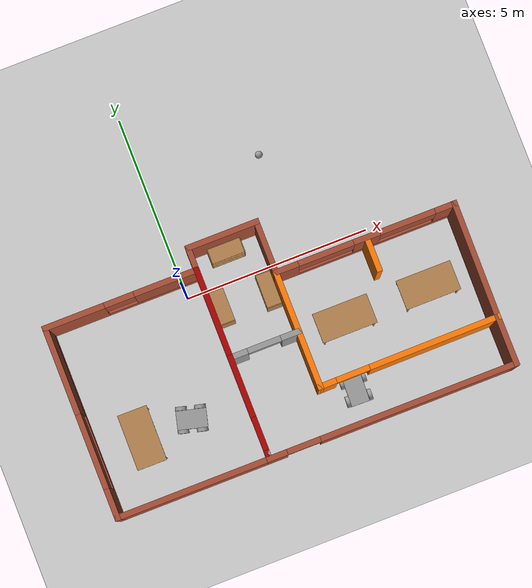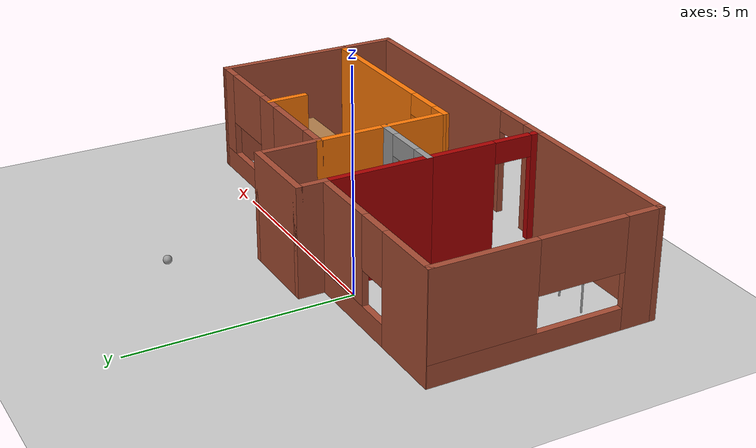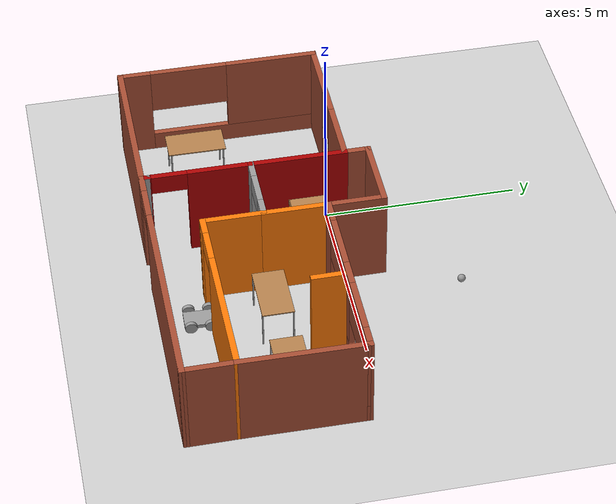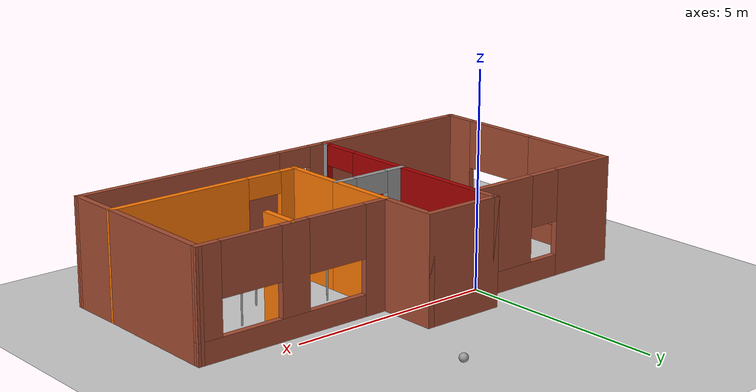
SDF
<sdf version="1.6">
 <world name="default">
  <plugin name="welcome_message" filename="libwelcome_message.so"/>
  <light name="sun" type="directional">
   <pose>0 0 10 0 -0 0</pose>
   <diffuse>0.8 0.8 0.8 1</diffuse>
   <specular>0.2 0.2 0.2 1</specular>
   <attenuation>
    <range>1000</range>
    <constant>0.9</constant>
    <linear>0.01</linear>
    <quadratic>0.001</quadratic>
   </attenuation>
   <direction>-0.5 0.1 -0.9</direction>
  </light>
  <model name="ground_plane">
   <static>1</static>
   <link name="link">
    <collision name="collision">
     <geometry><plane><normal>0 0 1</normal><size>100 100</size></plane></geometry>
     <surface><friction><ode><mu>100</mu><mu2>50</mu2></ode></friction></surface>
    </collision>
    <visual name="visual">
     <cast_shadows>0</cast_shadows>
     <geometry><plane><normal>0 0 1</normal><size>100 100</size></plane></geometry>
     <material>
      <script><uri>file://media/materials/scripts/gazebo.material</uri><name>Gazebo/Grey</name></script>
     </material>
    </visual>
   </link>
  </model>
  <gravity>0 0 -9.8</gravity>
  <magnetic_field>6e-06 2.3e-05 -4.2e-05</magnetic_field>
  <atmosphere type="adiabatic"/>
  <physics name="default_physics" default="0" type="ode">
   <max_step_size>0.001</max_step_size>
   <real_time_factor>1</real_time_factor>
   <real_time_update_rate>1000</real_time_update_rate>
  </physics>
  <scene><ambient>0.4 0.4 0.4 1</ambient><background>0.7 0.7 0.7 1</background><shadows>1</shadows></scene>
  <spherical_coordinates>
   <surface_model>EARTH_WGS84</surface_model>
   <latitude_deg>0</latitude_deg>
   <longitude_deg>0</longitude_deg>
   <elevation>0</elevation>
   <heading_deg>0</heading_deg>
  </spherical_coordinates>
  <model name="myhome">
   <pose>1.77518 -1.86888 0 0 -0 0</pose>
   <link name="Wall_21">
    <pose>-5.40037 -0.307409 0 0 -0 1.5708</pose>
    <visual name="Wall_21_Visual_0">
     <pose>-2.19882 0 1.25 0 -0 0</pose>
     <geometry><box><size>0.852368 0.15 2.5</size></box></geometry>
     <material>
      <script><uri>file://media/materials/scripts/gazebo.material</uri><name>Gazebo/Bricks</name></script>
      <ambient>0.666667 0 0 1</ambient>
     </material>
     <meta><layer>0</layer></meta>
    </visual>
    <collision name="Wall_21_Collision_0">
     <geometry><box><size>0.852368 0.15 2.5</size></box></geometry>
     <pose>-2.19882 0 1.25 0 -0 0</pose>
    </collision>
    <visual name="Wall_21_Visual_1">
     <pose>0.426184 0 0.25 0 -0 0</pose>
     <geometry><box><size>4.39763 0.15 0.5</size></box></geometry>
     <material>
      <script><uri>file://media/materials/scripts/gazebo.material</uri><name>Gazebo/Bricks</name></script>
      <ambient>0.666667 0 0 1</ambient>
     </material>
     <meta><layer>0</layer></meta>
    </visual>
    <collision name="Wall_21_Collision_1">
     <geometry><box><size>4.39763 0.15 0.5</size></box></geometry>
     <pose>0.426184 0 0.25 0 -0 0</pose>
    </collision>
    <visual name="Wall_21_Visual_2">
     <pose>1.42618 0 1.5 0 -0 0</pose>
     <geometry><box><size>2.39763 0.15 2</size></box></geometry>
     <material>
      <script><uri>file://media/materials/scripts/gazebo.material</uri><name>Gazebo/Bricks</name></script>
      <ambient>0.666667 0 0 1</ambient>
     </material>
     <meta><layer>0</layer></meta>
    </visual>
    <collision name="Wall_21_Collision_2">
     <geometry><box><size>2.39763 0.15 2</size></box></geometry>
     <pose>1.42618 0 1.5 0 -0 0</pose>
    </collision>
    <visual name="Wall_21_Visual_3">
     <pose>-0.772632 0 1.9 0 -0 0</pose>
     <geometry><box><size>2 0.15 1.2</size></box></geometry>
     <material>
      <script><uri>file://media/materials/scripts/gazebo.material</uri><name>Gazebo/Bricks</name></script>
      <ambient>0.666667 0 0 1</ambient>
     </material>
     <meta><layer>0</layer></meta>
    </visual>
    <collision name="Wall_21_Collision_3">
     <geometry><box><size>2 0.15 1.2</size></box></geometry>
     <pose>-0.772632 0 1.9 0 -0 0</pose>
    </collision>
   </link>
   <link name="Wall_49">
    <pose>-3.35037 2.2578 0 0 -0 0</pose>
    <visual name="Wall_49_Visual_0">
     <pose>-1.28919 0 1.25 0 -0 0</pose>
     <geometry><box><size>1.67163 0.15 2.5</size></box></geometry>
     <material>
      <script><uri>file://media/materials/scripts/gazebo.material</uri><name>Gazebo/Bricks</name></script>
      <ambient>1 1 1 1</ambient>
     </material>
     <meta><layer>0</layer></meta>
    </visual>
    <collision name="Wall_49_Collision_0">
     <geometry><box><size>1.67163 0.15 2.5</size></box></geometry>
     <pose>-1.28919 0 1.25 0 -0 0</pose>
    </collision>
    <visual name="Wall_49_Visual_1">
     <pose>0.835814 0 0.25 0 -0 0</pose>
     <geometry><box><size>2.57837 0.15 0.5</size></box></geometry>
     <material>
      <script><uri>file://media/materials/scripts/gazebo.material</uri><name>Gazebo/Bricks</name></script>
      <ambient>1 1 1 1</ambient>
     </material>
     <meta><layer>0</layer></meta>
    </visual>
    <collision name="Wall_49_Collision_1">
     <geometry><box><size>2.57837 0.15 0.5</size></box></geometry>
     <pose>0.835814 0 0.25 0 -0 0</pose>
    </collision>
    <visual name="Wall_49_Visual_2">
     <pose>1.23581 0 1.5 0 -0 0</pose>
     <geometry><box><size>1.77837 0.15 2</size></box></geometry>
     <material>
      <script><uri>file://media/materials/scripts/gazebo.material</uri><name>Gazebo/Bricks</name></script>
      <ambient>1 1 1 1</ambient>
     </material>
     <meta><layer>0</layer></meta>
    </visual>
    <collision name="Wall_49_Collision_2">
     <geometry><box><size>1.77837 0.15 2</size></box></geometry>
     <pose>1.23581 0 1.5 0 -0 0</pose>
    </collision>
    <visual name="Wall_49_Visual_3">
     <pose>-0.053373 0 1.9 0 -0 0</pose>
     <geometry><box><size>0.8 0.15 1.2</size></box></geometry>
     <material>
      <script><uri>file://media/materials/scripts/gazebo.material</uri><name>Gazebo/Bricks</name></script>
      <ambient>1 1 1 1</ambient>
     </material>
     <meta><layer>0</layer></meta>
    </visual>
    <collision name="Wall_49_Collision_3">
     <geometry><box><size>0.8 0.15 1.2</size></box></geometry>
     <pose>-0.053373 0 1.9 0 -0 0</pose>
    </collision>
   </link>
   <link name="Wall_50">
    <collision name="Wall_50_Collision">
     <geometry><box><size>2.53042 0.15 2.5</size></box></geometry>
     <pose>0 0 1.25 0 -0 0</pose>
    </collision>
    <visual name="Wall_50_Visual">
     <pose>0 0 1.25 0 -0 0</pose>
     <geometry><box><size>2.53042 0.15 2.5</size></box></geometry>
     <material>
      <script><uri>file://media/materials/scripts/gazebo.material</uri><name>Gazebo/Grey</name></script>
      <ambient>0.666667 0 0 1</ambient>
     </material>
     <meta><layer>0</layer></meta>
    </visual>
    <pose>-1.30037 1.06759 0 0 0 -1.5708</pose>
   </link>
   <link name="Wall_51">
    <pose>-0.37537 -0.122618 0 0 -0 0</pose>
    <visual name="Wall_51_Visual_0">
     <pose>-0.730669 0 1.25 0 -0 0</pose>
     <geometry><box><size>0.538663 0.15 2.5</size></box></geometry>
     <material>
      <script><uri>file://media/materials/scripts/gazebo.material</uri><name>Gazebo/Grey</name></script>
      <ambient>1 1 1 1</ambient>
     </material>
     <meta><layer>0</layer></meta>
    </visual>
    <collision name="Wall_51_Collision_0">
     <geometry><box><size>0.538663 0.15 2.5</size></box></geometry>
     <pose>-0.730669 0 1.25 0 -0 0</pose>
    </collision>
    <visual name="Wall_51_Visual_1">
     <pose>0.719331 0 1.25 0 -0 0</pose>
     <geometry><box><size>0.561337 0.15 2.5</size></box></geometry>
     <material>
      <script><uri>file://media/materials/scripts/gazebo.material</uri><name>Gazebo/Grey</name></script>
      <ambient>1 1 1 1</ambient>
     </material>
     <meta><layer>0</layer></meta>
    </visual>
    <collision name="Wall_51_Collision_1">
     <geometry><box><size>0.561337 0.15 2.5</size></box></geometry>
     <pose>0.719331 0 1.25 0 -0 0</pose>
    </collision>
    <visual name="Wall_51_Visual_2">
     <pose>-0.011337 0 2.25 0 -0 0</pose>
     <geometry><box><size>0.9 0.15 0.5</size></box></geometry>
     <material>
      <script><uri>file://media/materials/scripts/gazebo.material</uri><name>Gazebo/Grey</name></script>
      <ambient>1 1 1 1</ambient>
     </material>
     <meta><layer>0</layer></meta>
    </visual>
    <collision name="Wall_51_Collision_2">
     <geometry><box><size>0.9 0.15 0.5</size></box></geometry>
     <pose>-0.011337 0 2.25 0 -0 0</pose>
    </collision>
   </link>
   <link name="Wall_52">
    <collision name="Wall_52_Collision">
     <geometry><box><size>1.75 0.15 2.5</size></box></geometry>
     <pose>0 0 1.25 0 -0 0</pose>
    </collision>
    <visual name="Wall_52_Visual">
     <pose>0 0 1.25 0 -0 0</pose>
     <geometry><box><size>1.75 0.15 2.5</size></box></geometry>
     <material>
      <script><uri>file://media/materials/scripts/gazebo.material</uri><name>Gazebo/Grey</name></script>
      <ambient>0.996078 0.47451 0.0196078 1</ambient>
     </material>
     <meta><layer>0</layer></meta>
    </visual>
    <pose>0.54963 0.677382 0 0 -0 1.5708</pose>
   </link>
   <link name="Wall_53">
    <pose>2.97463 1.47738 0 0 -0 0</pose>
    <visual name="Wall_53_Visual_0">
     <pose>-2.15919 0 1.25 0 -0 0</pose>
     <geometry><box><size>0.68161 0.15 2.5</size></box></geometry>
     <material>
      <script><uri>file://media/materials/scripts/gazebo.material</uri><name>Gazebo/Bricks</name></script>
      <ambient>0.996078 0.47451 0.0196078 1</ambient>
     </material>
     <meta><layer>0</layer></meta>
    </visual>
    <collision name="Wall_53_Collision_0">
     <geometry><box><size>0.68161 0.15 2.5</size></box></geometry>
     <pose>-2.15919 0 1.25 0 -0 0</pose>
    </collision>
    <visual name="Wall_53_Visual_1">
     <pose>0.340805 0 0.25 0 -0 0</pose>
     <geometry><box><size>4.31839 0.15 0.5</size></box></geometry>
     <material>
      <script><uri>file://media/materials/scripts/gazebo.material</uri><name>Gazebo/Bricks</name></script>
      <ambient>0.996078 0.47451 0.0196078 1</ambient>
     </material>
     <meta><layer>0</layer></meta>
    </visual>
    <collision name="Wall_53_Collision_1">
     <geometry><box><size>4.31839 0.15 0.5</size></box></geometry>
     <pose>0.340805 0 0.25 0 -0 0</pose>
    </collision>
    <visual name="Wall_53_Visual_2">
     <pose>0.037857 0 1.5 0 -0 0</pose>
     <geometry><box><size>0.712493 0.15 2</size></box></geometry>
     <material>
      <script><uri>file://media/materials/scripts/gazebo.material</uri><name>Gazebo/Bricks</name></script>
      <ambient>0.996078 0.47451 0.0196078 1</ambient>
     </material>
     <meta><layer>0</layer></meta>
    </visual>
    <collision name="Wall_53_Collision_2">
     <geometry><box><size>0.712493 0.15 2</size></box></geometry>
     <pose>0.037857 0 1.5 0 -0 0</pose>
    </collision>
    <visual name="Wall_53_Visual_3">
     <pose>2.19705 0 1.5 0 -0 0</pose>
     <geometry><box><size>0.605897 0.15 2</size></box></geometry>
     <material>
      <script><uri>file://media/materials/scripts/gazebo.material</uri><name>Gazebo/Bricks</name></script>
      <ambient>0.996078 0.47451 0.0196078 1</ambient>
     </material>
     <meta><layer>0</layer></meta>
    </visual>
    <collision name="Wall_53_Collision_3">
     <geometry><box><size>0.605897 0.15 2</size></box></geometry>
     <pose>2.19705 0 1.5 0 -0 0</pose>
    </collision>
    <visual name="Wall_53_Visual_4">
     <pose>-1.06839 0 1.9 0 -0 0</pose>
     <geometry><box><size>1.5 0.15 1.2</size></box></geometry>
     <material>
      <script><uri>file://media/materials/scripts/gazebo.material</uri><name>Gazebo/Bricks</name></script>
      <ambient>0.996078 0.47451 0.0196078 1</ambient>
     </material>
     <meta><layer>0</layer></meta>
    </visual>
    <collision name="Wall_53_Collision_4">
     <geometry><box><size>1.5 0.15 1.2</size></box></geometry>
     <pose>-1.06839 0 1.9 0 -0 0</pose>
    </collision>
    <visual name="Wall_53_Visual_5">
     <pose>1.1441 0 1.9 0 -0 0</pose>
     <geometry><box><size>1.5 0.15 1.2</size></box></geometry>
     <material>
      <script><uri>file://media/materials/scripts/gazebo.material</uri><name>Gazebo/Bricks</name></script>
      <ambient>0.996078 0.47451 0.0196078 1</ambient>
     </material>
     <meta><layer>0</layer></meta>
    </visual>
    <collision name="Wall_53_Collision_5">
     <geometry><box><size>1.5 0.15 1.2</size></box></geometry>
     <pose>1.1441 0 1.9 0 -0 0</pose>
    </collision>
   </link>
   <link name="Wall_54">
    <collision name="Wall_54_Collision">
     <geometry><box><size>3.21992 0.15 2.5</size></box></geometry>
     <pose>0 0 1.25 0 -0 0</pose>
    </collision>
    <visual name="Wall_54_Visual">
     <pose>0 0 1.25 0 -0 0</pose>
     <geometry><box><size>3.21992 0.15 2.5</size></box></geometry>
     <material>
      <script><uri>file://media/materials/scripts/gazebo.material</uri><name>Gazebo/Bricks</name></script>
      <ambient>0.996078 0.47451 0.0196078 1</ambient>
     </material>
     <meta><layer>0</layer></meta>
    </visual>
    <pose>5.38442 -0.057409 0 0 0 -1.58071</pose>
   </link>
   <link name="Wall_55">
    <pose>2.95942 -1.60741 0 0 0 -3.13528</pose>
    <visual name="Wall_55_Visual_0">
     <pose>-0.706986 0 1.25 0 -0 0</pose>
     <geometry><box><size>3.55571 0.15 2.5</size></box></geometry>
     <material>
      <script><uri>file://media/materials/scripts/gazebo.material</uri><name>Gazebo/Grey</name></script>
      <ambient>0.996078 0.47451 0.0196078 1</ambient>
     </material>
     <meta><layer>0</layer></meta>
    </visual>
    <collision name="Wall_55_Collision_0">
     <geometry><box><size>3.55571 0.15 2.5</size></box></geometry>
     <pose>-0.706986 0 1.25 0 -0 0</pose>
    </collision>
    <visual name="Wall_55_Visual_1">
     <pose>2.22785 0 1.25 0 -0 0</pose>
     <geometry><box><size>0.513973 0.15 2.5</size></box></geometry>
     <material>
      <script><uri>file://media/materials/scripts/gazebo.material</uri><name>Gazebo/Grey</name></script>
      <ambient>0.996078 0.47451 0.0196078 1</ambient>
     </material>
     <meta><layer>0</layer></meta>
    </visual>
    <collision name="Wall_55_Collision_1">
     <geometry><box><size>0.513973 0.15 2.5</size></box></geometry>
     <pose>2.22785 0 1.25 0 -0 0</pose>
    </collision>
    <visual name="Wall_55_Visual_2">
     <pose>1.52087 0 2.25 0 -0 0</pose>
     <geometry><box><size>0.9 0.15 0.5</size></box></geometry>
     <material>
      <script><uri>file://media/materials/scripts/gazebo.material</uri><name>Gazebo/Grey</name></script>
      <ambient>0.996078 0.47451 0.0196078 1</ambient>
     </material>
     <meta><layer>0</layer></meta>
    </visual>
    <collision name="Wall_55_Collision_2">
     <geometry><box><size>0.9 0.15 0.5</size></box></geometry>
     <pose>1.52087 0 2.25 0 -0 0</pose>
    </collision>
   </link>
   <link name="Wall_56">
    <collision name="Wall_56_Collision">
     <geometry><box><size>1.65 0.15 2.5</size></box></geometry>
     <pose>0 0 1.25 0 -0 0</pose>
    </collision>
    <visual name="Wall_56_Visual">
     <pose>0 0 1.25 0 -0 0</pose>
     <geometry><box><size>1.65 0.15 2.5</size></box></geometry>
     <material>
      <script><uri>file://media/materials/scripts/gazebo.material</uri><name>Gazebo/Grey</name></script>
      <ambient>0.996078 0.47451 0.0196078 1</ambient>
     </material>
     <meta><layer>0</layer></meta>
    </visual>
    <pose>0.54963 -0.872618 0 0 -0 1.5708</pose>
   </link>
   <link name="Wall_64">
    <collision name="Wall_64_Collision">
     <geometry><box><size>1.41536 0.15 2.5</size></box></geometry>
     <pose>0 0 1.25 0 -0 0</pose>
    </collision>
    <visual name="Wall_64_Visual">
     <pose>0 0 1.25 0 -0 0</pose>
     <geometry><box><size>1.41536 0.15 2.5</size></box></geometry>
     <material>
      <script><uri>file://media/materials/scripts/gazebo.material</uri><name>Gazebo/Bricks</name></script>
      <ambient>1 1 1 1</ambient>
     </material>
     <meta><layer>0</layer></meta>
    </visual>
    <pose>5.37192 -2.2248 0 0 -0 1.57508</pose>
   </link>
   <link name="Wall_71">
    <collision name="Wall_71_Collision">
     <geometry><box><size>0.75 0.15 2.5</size></box></geometry>
     <pose>0 0 1.25 0 -0 0</pose>
    </collision>
    <visual name="Wall_71_Visual">
     <pose>0 0 1.25 0 -0 0</pose>
     <geometry><box><size>0.75 0.15 2.5</size></box></geometry>
     <material>
      <script><uri>file://media/materials/scripts/gazebo.material</uri><name>Gazebo/Bricks</name></script>
      <ambient>1 1 1 1</ambient>
     </material>
     <meta><layer>0</layer></meta>
    </visual>
    <pose>-1.30037 2.5578 0 0 -0 1.5708</pose>
   </link>
   <link name="Wall_72">
    <collision name="Wall_72_Collision">
     <geometry><box><size>2 0.15 2.5</size></box></geometry>
     <pose>0 0 1.25 0 -0 0</pose>
    </collision>
    <visual name="Wall_72_Visual">
     <pose>0 0 1.25 0 -0 0</pose>
     <geometry><box><size>2 0.15 2.5</size></box></geometry>
     <material>
      <script><uri>file://media/materials/scripts/gazebo.material</uri><name>Gazebo/Bricks</name></script>
      <ambient>1 1 1 1</ambient>
     </material>
     <meta><layer>0</layer></meta>
    </visual>
    <pose>-0.37537 2.8578 0 0 -0 0</pose>
   </link>
   <link name="Wall_73">
    <collision name="Wall_73_Collision">
     <geometry><box><size>1.53042 0.15 2.5</size></box></geometry>
     <pose>0 0 1.25 0 -0 0</pose>
    </collision>
    <visual name="Wall_73_Visual">
     <pose>0 0 1.25 0 -0 0</pose>
     <geometry><box><size>1.53042 0.15 2.5</size></box></geometry>
     <material>
      <script><uri>file://media/materials/scripts/gazebo.material</uri><name>Gazebo/Bricks</name></script>
      <ambient>1 1 1 1</ambient>
     </material>
     <meta><layer>0</layer></meta>
    </visual>
    <pose>0.54963 2.16759 0 0 0 -1.5708</pose>
   </link>
   <link name="Wall_75">
    <collision name="Wall_75_Collision">
     <geometry><box><size>1 0.15 2.5</size></box></geometry>
     <pose>0 0 1.25 0 -0 0</pose>
    </collision>
    <visual name="Wall_75_Visual">
     <pose>0 0 1.25 0 -0 0</pose>
     <geometry><box><size>1 0.15 2.5</size></box></geometry>
     <material>
      <script><uri>file://media/materials/scripts/gazebo.material</uri><name>Gazebo/Grey</name></script>
      <ambient>0.996078 0.47451 0.0196078 1</ambient>
     </material>
     <meta><layer>0</layer></meta>
    </visual>
    <pose>3.01249 1.04938 0 0 0 -1.5708</pose>
   </link>
   <link name="Wall_82">
    <pose>-1.30037 -1.42262 0 0 0 -1.5708</pose>
    <visual name="Wall_82_Visual_0">
     <pose>-0.536175 0 1.25 0 -0 0</pose>
     <geometry><box><size>1.67765 0.15 2.5</size></box></geometry>
     <material>
      <script><uri>file://media/materials/scripts/gazebo.material</uri><name>Gazebo/Grey</name></script>
      <ambient>0.666667 0 0 1</ambient>
     </material>
     <meta><layer>0</layer></meta>
    </visual>
    <collision name="Wall_82_Collision_0">
     <geometry><box><size>1.67765 0.15 2.5</size></box></geometry>
     <pose>-0.536175 0 1.25 0 -0 0</pose>
    </collision>
    <visual name="Wall_82_Visual_1">
     <pose>1.28883 0 1.25 0 -0 0</pose>
     <geometry><box><size>0.172351 0.15 2.5</size></box></geometry>
     <material>
      <script><uri>file://media/materials/scripts/gazebo.material</uri><name>Gazebo/Grey</name></script>
      <ambient>0.666667 0 0 1</ambient>
     </material>
     <meta><layer>0</layer></meta>
    </visual>
    <collision name="Wall_82_Collision_1">
     <geometry><box><size>0.172351 0.15 2.5</size></box></geometry>
     <pose>1.28883 0 1.25 0 -0 0</pose>
    </collision>
    <visual name="Wall_82_Visual_2">
     <pose>0.752649 0 2.25 0 -0 0</pose>
     <geometry><box><size>0.9 0.15 0.5</size></box></geometry>
     <material>
      <script><uri>file://media/materials/scripts/gazebo.material</uri><name>Gazebo/Grey</name></script>
      <ambient>0.666667 0 0 1</ambient>
     </material>
     <meta><layer>0</layer></meta>
    </visual>
    <collision name="Wall_82_Collision_2">
     <geometry><box><size>0.9 0.15 0.5</size></box></geometry>
     <pose>0.752649 0 2.25 0 -0 0</pose>
    </collision>
   </link>
   <link name="Wall_83">
    <collision name="Wall_83_Collision">
     <geometry><box><size>0.15 0.15 2.5</size></box></geometry>
     <pose>0 0 1.25 0 -0 0</pose>
    </collision>
    <visual name="Wall_83_Visual">
     <pose>0 0 1.25 0 -0 0</pose>
     <geometry><box><size>0.15 0.15 2.5</size></box></geometry>
     <material>
      <script><uri>file://media/materials/scripts/gazebo.material</uri><name>Gazebo/Grey</name></script>
      <ambient>1 1 1 1</ambient>
     </material>
     <meta><layer>0</layer></meta>
    </visual>
    <pose>-1.30037 -2.72262 0 0 -0 0</pose>
   </link>
   <link name="Wall_85">
    <collision name="Wall_85_Collision">
     <geometry><box><size>4.25 0.15 2.5</size></box></geometry>
     <pose>0 0 1.25 0 -0 0</pose>
    </collision>
    <visual name="Wall_85_Visual">
     <pose>0 0 1.25 0 -0 0</pose>
     <geometry><box><size>4.25 0.15 2.5</size></box></geometry>
     <material>
      <script><uri>file://media/materials/scripts/gazebo.material</uri><name>Gazebo/Bricks</name></script>
      <ambient>1 1 1 1</ambient>
     </material>
     <meta><layer>0</layer></meta>
    </visual>
    <pose>-3.35037 -2.85741 0 0 -0 0</pose>
   </link>
   <link name="Wall_86">
    <pose>2.03713 -2.85741 0 0 -0 0</pose>
    <visual name="Wall_86_Visual_0">
     <pose>-3.1352 0 1.25 0 -0 0</pose>
     <geometry><box><size>0.554602 0.15 2.5</size></box></geometry>
     <material>
      <script><uri>file://media/materials/scripts/gazebo.material</uri><name>Gazebo/Bricks</name></script>
      <ambient>1 1 1 1</ambient>
     </material>
     <meta><layer>0</layer></meta>
    </visual>
    <collision name="Wall_86_Collision_0">
     <geometry><box><size>0.554602 0.15 2.5</size></box></geometry>
     <pose>-3.1352 0 1.25 0 -0 0</pose>
    </collision>
    <visual name="Wall_86_Visual_1">
     <pose>0.727301 0 1.25 0 -0 0</pose>
     <geometry><box><size>5.3704 0.15 2.5</size></box></geometry>
     <material>
      <script><uri>file://media/materials/scripts/gazebo.material</uri><name>Gazebo/Bricks</name></script>
      <ambient>1 1 1 1</ambient>
     </material>
     <meta><layer>0</layer></meta>
    </visual>
    <collision name="Wall_86_Collision_1">
     <geometry><box><size>5.3704 0.15 2.5</size></box></geometry>
     <pose>0.727301 0 1.25 0 -0 0</pose>
    </collision>
    <visual name="Wall_86_Visual_2">
     <pose>-2.4079 0 2.25 0 -0 0</pose>
     <geometry><box><size>0.9 0.15 0.5</size></box></geometry>
     <material>
      <script><uri>file://media/materials/scripts/gazebo.material</uri><name>Gazebo/Bricks</name></script>
      <ambient>1 1 1 1</ambient>
     </material>
     <meta><layer>0</layer></meta>
    </visual>
    <collision name="Wall_86_Collision_2">
     <geometry><box><size>0.9 0.15 0.5</size></box></geometry>
     <pose>-2.4079 0 2.25 0 -0 0</pose>
    </collision>
   </link>
   <static>1</static>
  </model>
  <model name="bookshelf">
   <static>1</static>
   <link name="link">
    <inertial><mass>1</mass></inertial>
    <collision name="back">
     <pose>0 0.005 0.6 0 -0 0</pose>
     <geometry><box><size>0.9 0.01 1.2</size></box></geometry>
    </collision>
    <visual name="visual1">
     <pose>0 0.005 0.6 0 -0 0</pose>
     <geometry><box><size>0.9 0.01 1.2</size></box></geometry>
     <material>
      <script><uri>file://media/materials/scripts/gazebo.material</uri><name>Gazebo/Wood</name></script>
     </material>
    </visual>
    <collision name="left_side">
     <pose>0.45 -0.195 0.6 0 -0 0</pose>
     <geometry><box><size>0.02 0.4 1.2</size></box></geometry>
    </collision>
    <visual name="visual2">
     <pose>0.45 -0.195 0.6 0 -0 0</pose>
     <geometry><box><size>0.02 0.4 1.2</size></box></geometry>
     <material>
      <script><uri>file://media/materials/scripts/gazebo.material</uri><name>Gazebo/Wood</name></script>
     </material>
    </visual>
    <collision name="right_side">
     <pose>-0.45 -0.195 0.6 0 -0 0</pose>
     <geometry><box><size>0.02 0.4 1.2</size></box></geometry>
    </collision>
    <visual name="visual3">
     <pose>-0.45 -0.195 0.6 0 -0 0</pose>
     <geometry><box><size>0.02 0.4 1.2</size></box></geometry>
     <material>
      <script><uri>file://media/materials/scripts/gazebo.material</uri><name>Gazebo/Wood</name></script>
     </material>
    </visual>
    <collision name="bottom">
     <pose>0 -0.195 0.03 0 -0 0</pose>
     <geometry><box><size>0.88 0.4 0.06</size></box></geometry>
    </collision>
    <visual name="visual4">
     <pose>0 -0.195 0.03 0 -0 0</pose>
     <geometry><box><size>0.88 0.4 0.06</size></box></geometry>
     <material>
      <script><uri>file://media/materials/scripts/gazebo.material</uri><name>Gazebo/Wood</name></script>
     </material>
    </visual>
    <collision name="top">
     <pose>0 -0.195 1.19 0 -0 0</pose>
     <geometry><box><size>0.88 0.4 0.02</size></box></geometry>
    </collision>
    <visual name="visual5">
     <pose>0 -0.195 1.19 0 -0 0</pose>
     <geometry><box><size>0.88 0.4 0.02</size></box></geometry>
     <material>
      <script><uri>file://media/materials/scripts/gazebo.material</uri><name>Gazebo/Wood</name></script>
     </material>
    </visual>
    <collision name="low_shelf">
     <pose>0 -0.195 0.43 0 -0 0</pose>
     <geometry><box><size>0.88 0.4 0.02</size></box></geometry>
    </collision>
    <visual name="visual6">
     <pose>0 -0.195 0.43 0 -0 0</pose>
     <geometry><box><size>0.88 0.4 0.02</size></box></geometry>
     <material>
      <script><uri>file://media/materials/scripts/gazebo.material</uri><name>Gazebo/Wood</name></script>
     </material>
    </visual>
    <collision name="high_shelf">
     <pose>0 -0.195 0.8 0 -0 0</pose>
     <geometry><box><size>0.88 0.4 0.02</size></box></geometry>
    </collision>
    <visual name="visual7">
     <pose>0 -0.195 0.8 0 -0 0</pose>
     <geometry><box><size>0.88 0.4 0.02</size></box></geometry>
     <material>
      <script><uri>file://media/materials/scripts/gazebo.material</uri><name>Gazebo/Wood</name></script>
     </material>
    </visual>
   </link>
   <pose>1.36245 0.894727 0 0 -0 0</pose>
  </model>
  <model name="bookshelf_0">
   <static>1</static>
   <link name="link">
    <inertial><mass>1</mass></inertial>
    <collision name="back">
     <pose>0 0.005 0.6 0 -0 0</pose>
     <geometry><box><size>0.9 0.01 1.2</size></box></geometry>
    </collision>
    <visual name="visual1">
     <pose>0 0.005 0.6 0 -0 0</pose>
     <geometry><box><size>0.9 0.01 1.2</size></box></geometry>
     <material>
      <script><uri>file://media/materials/scripts/gazebo.material</uri><name>Gazebo/Wood</name></script>
     </material>
    </visual>
    <collision name="left_side">
     <pose>0.45 -0.195 0.6 0 -0 0</pose>
     <geometry><box><size>0.02 0.4 1.2</size></box></geometry>
    </collision>
    <visual name="visual2">
     <pose>0.45 -0.195 0.6 0 -0 0</pose>
     <geometry><box><size>0.02 0.4 1.2</size></box></geometry>
     <material>
      <script><uri>file://media/materials/scripts/gazebo.material</uri><name>Gazebo/Wood</name></script>
     </material>
    </visual>
    <collision name="right_side">
     <pose>-0.45 -0.195 0.6 0 -0 0</pose>
     <geometry><box><size>0.02 0.4 1.2</size></box></geometry>
    </collision>
    <visual name="visual3">
     <pose>-0.45 -0.195 0.6 0 -0 0</pose>
     <geometry><box><size>0.02 0.4 1.2</size></box></geometry>
     <material>
      <script><uri>file://media/materials/scripts/gazebo.material</uri><name>Gazebo/Wood</name></script>
     </material>
    </visual>
    <collision name="bottom">
     <pose>0 -0.195 0.03 0 -0 0</pose>
     <geometry><box><size>0.88 0.4 0.06</size></box></geometry>
    </collision>
    <visual name="visual4">
     <pose>0 -0.195 0.03 0 -0 0</pose>
     <geometry><box><size>0.88 0.4 0.06</size></box></geometry>
     <material>
      <script><uri>file://media/materials/scripts/gazebo.material</uri><name>Gazebo/Wood</name></script>
     </material>
    </visual>
    <collision name="top">
     <pose>0 -0.195 1.19 0 -0 0</pose>
     <geometry><box><size>0.88 0.4 0.02</size></box></geometry>
    </collision>
    <visual name="visual5">
     <pose>0 -0.195 1.19 0 -0 0</pose>
     <geometry><box><size>0.88 0.4 0.02</size></box></geometry>
     <material>
      <script><uri>file://media/materials/scripts/gazebo.material</uri><name>Gazebo/Wood</name></script>
     </material>
    </visual>
    <collision name="low_shelf">
     <pose>0 -0.195 0.43 0 -0 0</pose>
     <geometry><box><size>0.88 0.4 0.02</size></box></geometry>
    </collision>
    <visual name="visual6">
     <pose>0 -0.195 0.43 0 -0 0</pose>
     <geometry><box><size>0.88 0.4 0.02</size></box></geometry>
     <material>
      <script><uri>file://media/materials/scripts/gazebo.material</uri><name>Gazebo/Wood</name></script>
     </material>
    </visual>
    <collision name="high_shelf">
     <pose>0 -0.195 0.8 0 -0 0</pose>
     <geometry><box><size>0.88 0.4 0.02</size></box></geometry>
    </collision>
    <visual name="visual7">
     <pose>0 -0.195 0.8 0 -0 0</pose>
     <geometry><box><size>0.88 0.4 0.02</size></box></geometry>
     <material>
      <script><uri>file://media/materials/scripts/gazebo.material</uri><name>Gazebo/Wood</name></script>
     </material>
    </visual>
   </link>
   <pose>0.54884 -0.601497 0 0 -0 1.56747</pose>
  </model>
  <model name="bookshelf_1">
   <static>1</static>
   <link name="link">
    <inertial><mass>1</mass></inertial>
    <collision name="back">
     <pose>0 0.005 0.6 0 -0 0</pose>
     <geometry><box><size>0.9 0.01 1.2</size></box></geometry>
    </collision>
    <visual name="visual1">
     <pose>0 0.005 0.6 0 -0 0</pose>
     <geometry><box><size>0.9 0.01 1.2</size></box></geometry>
     <material>
      <script><uri>file://media/materials/scripts/gazebo.material</uri><name>Gazebo/Wood</name></script>
     </material>
    </visual>
    <collision name="left_side">
     <pose>0.45 -0.195 0.6 0 -0 0</pose>
     <geometry><box><size>0.02 0.4 1.2</size></box></geometry>
    </collision>
    <visual name="visual2">
     <pose>0.45 -0.195 0.6 0 -0 0</pose>
     <geometry><box><size>0.02 0.4 1.2</size></box></geometry>
     <material>
      <script><uri>file://media/materials/scripts/gazebo.material</uri><name>Gazebo/Wood</name></script>
     </material>
    </visual>
    <collision name="right_side">
     <pose>-0.45 -0.195 0.6 0 -0 0</pose>
     <geometry><box><size>0.02 0.4 1.2</size></box></geometry>
    </collision>
    <visual name="visual3">
     <pose>-0.45 -0.195 0.6 0 -0 0</pose>
     <geometry><box><size>0.02 0.4 1.2</size></box></geometry>
     <material>
      <script><uri>file://media/materials/scripts/gazebo.material</uri><name>Gazebo/Wood</name></script>
     </material>
    </visual>
    <collision name="bottom">
     <pose>0 -0.195 0.03 0 -0 0</pose>
     <geometry><box><size>0.88 0.4 0.06</size></box></geometry>
    </collision>
    <visual name="visual4">
     <pose>0 -0.195 0.03 0 -0 0</pose>
     <geometry><box><size>0.88 0.4 0.06</size></box></geometry>
     <material>
      <script><uri>file://media/materials/scripts/gazebo.material</uri><name>Gazebo/Wood</name></script>
     </material>
    </visual>
    <collision name="top">
     <pose>0 -0.195 1.19 0 -0 0</pose>
     <geometry><box><size>0.88 0.4 0.02</size></box></geometry>
    </collision>
    <visual name="visual5">
     <pose>0 -0.195 1.19 0 -0 0</pose>
     <geometry><box><size>0.88 0.4 0.02</size></box></geometry>
     <material>
      <script><uri>file://media/materials/scripts/gazebo.material</uri><name>Gazebo/Wood</name></script>
     </material>
    </visual>
    <collision name="low_shelf">
     <pose>0 -0.195 0.43 0 -0 0</pose>
     <geometry><box><size>0.88 0.4 0.02</size></box></geometry>
    </collision>
    <visual name="visual6">
     <pose>0 -0.195 0.43 0 -0 0</pose>
     <geometry><box><size>0.88 0.4 0.02</size></box></geometry>
     <material>
      <script><uri>file://media/materials/scripts/gazebo.material</uri><name>Gazebo/Wood</name></script>
     </material>
    </visual>
    <collision name="high_shelf">
     <pose>0 -0.195 0.8 0 -0 0</pose>
     <geometry><box><size>0.88 0.4 0.02</size></box></geometry>
    </collision>
    <visual name="visual7">
     <pose>0 -0.195 0.8 0 -0 0</pose>
     <geometry><box><size>0.88 0.4 0.02</size></box></geometry>
     <material>
      <script><uri>file://media/materials/scripts/gazebo.material</uri><name>Gazebo/Wood</name></script>
     </material>
    </visual>
   </link>
   <pose>2.2247 -0.625547 0 0 0 -1.58004</pose>
  </model>
  <model name="table">
   <static>1</static>
   <link name="link">
    <collision name="surface">
     <pose>0 0 1 0 -0 0</pose>
     <geometry><box><size>1.5 0.8 0.03</size></box></geometry>
     <surface><friction><ode><mu>0.6</mu><mu2>0.6</mu2></ode></friction></surface>
    </collision>
    <visual name="visual1">
     <pose>0 0 1 0 -0 0</pose>
     <geometry><box><size>1.5 0.8 0.03</size></box></geometry>
     <material>
      <script><uri>file://media/materials/scripts/gazebo.material</uri><name>Gazebo/Wood</name></script>
     </material>
    </visual>
    <collision name="front_left_leg">
     <pose>0.68 0.38 0.5 0 -0 0</pose>
     <geometry><cylinder><radius>0.02</radius><length>1</length></cylinder></geometry>
    </collision>
    <visual name="front_left_leg">
     <pose>0.68 0.38 0.5 0 -0 0</pose>
     <geometry><cylinder><radius>0.02</radius><length>1</length></cylinder></geometry>
     <material>
      <script><uri>file://media/materials/scripts/gazebo.material</uri><name>Gazebo/Grey</name></script>
     </material>
    </visual>
    <collision name="front_right_leg">
     <pose>0.68 -0.38 0.5 0 -0 0</pose>
     <geometry><cylinder><radius>0.02</radius><length>1</length></cylinder></geometry>
    </collision>
    <visual name="front_right_leg">
     <pose>0.68 -0.38 0.5 0 -0 0</pose>
     <geometry><cylinder><radius>0.02</radius><length>1</length></cylinder></geometry>
     <material>
      <script><uri>file://media/materials/scripts/gazebo.material</uri><name>Gazebo/Grey</name></script>
     </material>
    </visual>
    <collision name="back_right_leg">
     <pose>-0.68 -0.38 0.5 0 -0 0</pose>
     <geometry><cylinder><radius>0.02</radius><length>1</length></cylinder></geometry>
    </collision>
    <visual name="back_right_leg">
     <pose>-0.68 -0.38 0.5 0 -0 0</pose>
     <geometry><cylinder><radius>0.02</radius><length>1</length></cylinder></geometry>
     <material>
      <script><uri>file://media/materials/scripts/gazebo.material</uri><name>Gazebo/Grey</name></script>
     </material>
    </visual>
    <collision name="back_left_leg">
     <pose>-0.68 0.38 0.5 0 -0 0</pose>
     <geometry><cylinder><radius>0.02</radius><length>1</length></cylinder></geometry>
    </collision>
    <visual name="back_left_leg">
     <pose>-0.68 0.38 0.5 0 -0 0</pose>
     <geometry><cylinder><radius>0.02</radius><length>1</length></cylinder></geometry>
     <material>
      <script><uri>file://media/materials/scripts/gazebo.material</uri><name>Gazebo/Grey</name></script>
     </material>
    </visual>
   </link>
   <pose>-2.37664 -3.00957 0 0 0 -1.57607</pose>
  </model>
  <model name="table_0">
   <static>1</static>
   <link name="link">
    <collision name="surface">
     <pose>0 0 1 0 -0 0</pose>
     <geometry><box><size>1.5 0.8 0.03</size></box></geometry>
     <surface><friction><ode><mu>0.6</mu><mu2>0.6</mu2></ode></friction></surface>
    </collision>
    <visual name="visual1">
     <pose>0 0 1 0 -0 0</pose>
     <geometry><box><size>1.5 0.8 0.03</size></box></geometry>
     <material>
      <script><uri>file://media/materials/scripts/gazebo.material</uri><name>Gazebo/Wood</name></script>
     </material>
    </visual>
    <collision name="front_left_leg">
     <pose>0.68 0.38 0.5 0 -0 0</pose>
     <geometry><cylinder><radius>0.02</radius><length>1</length></cylinder></geometry>
    </collision>
    <visual name="front_left_leg">
     <pose>0.68 0.38 0.5 0 -0 0</pose>
     <geometry><cylinder><radius>0.02</radius><length>1</length></cylinder></geometry>
     <material>
      <script><uri>file://media/materials/scripts/gazebo.material</uri><name>Gazebo/Grey</name></script>
     </material>
    </visual>
    <collision name="front_right_leg">
     <pose>0.68 -0.38 0.5 0 -0 0</pose>
     <geometry><cylinder><radius>0.02</radius><length>1</length></cylinder></geometry>
    </collision>
    <visual name="front_right_leg">
     <pose>0.68 -0.38 0.5 0 -0 0</pose>
     <geometry><cylinder><radius>0.02</radius><length>1</length></cylinder></geometry>
     <material>
      <script><uri>file://media/materials/scripts/gazebo.material</uri><name>Gazebo/Grey</name></script>
     </material>
    </visual>
    <collision name="back_right_leg">
     <pose>-0.68 -0.38 0.5 0 -0 0</pose>
     <geometry><cylinder><radius>0.02</radius><length>1</length></cylinder></geometry>
    </collision>
    <visual name="back_right_leg">
     <pose>-0.68 -0.38 0.5 0 -0 0</pose>
     <geometry><cylinder><radius>0.02</radius><length>1</length></cylinder></geometry>
     <material>
      <script><uri>file://media/materials/scripts/gazebo.material</uri><name>Gazebo/Grey</name></script>
     </material>
    </visual>
    <collision name="back_left_leg">
     <pose>-0.68 0.38 0.5 0 -0 0</pose>
     <geometry><cylinder><radius>0.02</radius><length>1</length></cylinder></geometry>
    </collision>
    <visual name="back_left_leg">
     <pose>-0.68 0.38 0.5 0 -0 0</pose>
     <geometry><cylinder><radius>0.02</radius><length>1</length></cylinder></geometry>
     <material>
      <script><uri>file://media/materials/scripts/gazebo.material</uri><name>Gazebo/Grey</name></script>
     </material>
    </visual>
   </link>
   <pose>3.59261 -2.02108 0 0 -0 0</pose>
  </model>
  <model name="table_1">
   <static>1</static>
   <link name="link">
    <collision name="surface">
     <pose>0 0 1 0 -0 0</pose>
     <geometry><box><size>1.5 0.8 0.03</size></box></geometry>
     <surface><friction><ode><mu>0.6</mu><mu2>0.6</mu2></ode></friction></surface>
    </collision>
    <visual name="visual1">
     <pose>0 0 1 0 -0 0</pose>
     <geometry><box><size>1.5 0.8 0.03</size></box></geometry>
     <material>
      <script><uri>file://media/materials/scripts/gazebo.material</uri><name>Gazebo/Wood</name></script>
     </material>
    </visual>
    <collision name="front_left_leg">
     <pose>0.68 0.38 0.5 0 -0 0</pose>
     <geometry><cylinder><radius>0.02</radius><length>1</length></cylinder></geometry>
    </collision>
    <visual name="front_left_leg">
     <pose>0.68 0.38 0.5 0 -0 0</pose>
     <geometry><cylinder><radius>0.02</radius><length>1</length></cylinder></geometry>
     <material>
      <script><uri>file://media/materials/scripts/gazebo.material</uri><name>Gazebo/Grey</name></script>
     </material>
    </visual>
    <collision name="front_right_leg">
     <pose>0.68 -0.38 0.5 0 -0 0</pose>
     <geometry><cylinder><radius>0.02</radius><length>1</length></cylinder></geometry>
    </collision>
    <visual name="front_right_leg">
     <pose>0.68 -0.38 0.5 0 -0 0</pose>
     <geometry><cylinder><radius>0.02</radius><length>1</length></cylinder></geometry>
     <material>
      <script><uri>file://media/materials/scripts/gazebo.material</uri><name>Gazebo/Grey</name></script>
     </material>
    </visual>
    <collision name="back_right_leg">
     <pose>-0.68 -0.38 0.5 0 -0 0</pose>
     <geometry><cylinder><radius>0.02</radius><length>1</length></cylinder></geometry>
    </collision>
    <visual name="back_right_leg">
     <pose>-0.68 -0.38 0.5 0 -0 0</pose>
     <geometry><cylinder><radius>0.02</radius><length>1</length></cylinder></geometry>
     <material>
      <script><uri>file://media/materials/scripts/gazebo.material</uri><name>Gazebo/Grey</name></script>
     </material>
    </visual>
    <collision name="back_left_leg">
     <pose>-0.68 0.38 0.5 0 -0 0</pose>
     <geometry><cylinder><radius>0.02</radius><length>1</length></cylinder></geometry>
    </collision>
    <visual name="back_left_leg">
     <pose>-0.68 0.38 0.5 0 -0 0</pose>
     <geometry><cylinder><radius>0.02</radius><length>1</length></cylinder></geometry>
     <material>
      <script><uri>file://media/materials/scripts/gazebo.material</uri><name>Gazebo/Grey</name></script>
     </material>
    </visual>
   </link>
   <pose>5.91265 -1.99673 0 0 -0 0</pose>
  </model>
  <model name="car_bot">
   <link name="link">
    <pose>0 0 0.2 0 -0 0</pose>
    <inertial>
     <mass>1</mass>
     <inertia>
      <ixx>0.166667</ixx>
      <ixy>0</ixy>
      <ixz>0</ixz>
      <iyy>0.166667</iyy>
      <iyz>0</iyz>
      <izz>0.166667</izz>
     </inertia>
    </inertial>
    <visual name="visual">
     <geometry><box><size>0.8 0.5 0.1</size></box></geometry>
     <material>
      <script><name>Gazebo/Grey</name><uri>file://media/materials/scripts/gazebo.material</uri></script>
      <shader type="pixel"><normal_map>__default__</normal_map></shader>
      <ambient>0.3 0.3 0.3 1</ambient>
      <diffuse>0.7 0.7 0.7 1</diffuse>
      <specular>0.01 0.01 0.01 1</specular>
      <emissive>0 0 0 1</emissive>
     </material>
    </visual>
    <collision name="collision">
     <geometry><box><size>0.8 0.5 0.1</size></box></geometry>
     <surface>
      <friction>
       <ode><mu>1</mu><mu2>1</mu2><fdir1>0 0 0</fdir1><slip1>0</slip1><slip2>0</slip2></ode>
       <torsional>
        <coefficient>1</coefficient>
        <patch_radius>0</patch_radius>
        <surface_radius>0</surface_radius>
        <use_patch_radius>1</use_patch_radius>
        <ode><slip>0</slip></ode>
       </torsional>
      </friction>
      <bounce><restitution_coefficient>0</restitution_coefficient><threshold>1e+06</threshold></bounce>
      <contact>
       <collide_without_contact>0</collide_without_contact>
       <collide_without_contact_bitmask>1</collide_without_contact_bitmask>
       <collide_bitmask>1</collide_bitmask>
       <ode>
        <soft_cfm>0</soft_cfm>
        <soft_erp>0.2</soft_erp>
        <kp>1e+13</kp>
        <kd>1</kd>
        <max_vel>0.01</max_vel>
        <min_depth>0</min_depth>
       </ode>
       <bullet>
        <split_impulse>1</split_impulse>
        <split_impulse_penetration_threshold>-0.01</split_impulse_penetration_threshold>
        <soft_cfm>0</soft_cfm>
        <soft_erp>0.2</soft_erp>
        <kp>1e+13</kp>
        <kd>1</kd>
       </bullet>
      </contact>
     </surface>
    </collision>
   </link>
   <link name="link_1">
    <pose>-0.25 -0.30063 0.245186 1.575 -0 0</pose>
    <inertial>
     <mass>1</mass>
     <inertia><ixx>0.145833</ixx><ixy>0</ixy><ixz>0</ixz><iyy>0.145833</iyy><iyz>0</iyz><izz>0.125</izz></inertia>
    </inertial>
    <visual name="visual">
     <geometry><cylinder><radius>0.15</radius><length>0.1</length></cylinder></geometry>
     <material>
      <lighting>1</lighting>
      <script><uri>file://media/materials/scripts/gazebo.material</uri><name>Gazebo/Grey</name></script>
      <shader type="pixel"><normal_map>__default__</normal_map></shader>
      <ambient>0.3 0.3 0.3 1</ambient>
      <diffuse>0.7 0.7 0.7 1</diffuse>
      <specular>0.01 0.01 0.01 1</specular>
      <emissive>0 0 0 1</emissive>
     </material>
    </visual>
    <collision name="collision">
     <geometry><cylinder><radius>0.15</radius><length>0.1</length></cylinder></geometry>
     <surface>
      <friction>
       <ode><mu>1</mu><mu2>1</mu2><fdir1>0 0 0</fdir1><slip1>0</slip1><slip2>0</slip2></ode>
       <torsional>
        <coefficient>1</coefficient>
        <patch_radius>0</patch_radius>
        <surface_radius>0</surface_radius>
        <use_patch_radius>1</use_patch_radius>
        <ode><slip>0</slip></ode>
       </torsional>
      </friction>
      <bounce><restitution_coefficient>0</restitution_coefficient><threshold>1e+06</threshold></bounce>
      <contact>
       <collide_without_contact>0</collide_without_contact>
       <collide_without_contact_bitmask>1</collide_without_contact_bitmask>
       <collide_bitmask>1</collide_bitmask>
       <ode>
        <soft_cfm>0</soft_cfm>
        <soft_erp>0.2</soft_erp>
        <kp>1e+13</kp>
        <kd>1</kd>
        <max_vel>0.01</max_vel>
        <min_depth>0</min_depth>
       </ode>
       <bullet>
        <split_impulse>1</split_impulse>
        <split_impulse_penetration_threshold>-0.01</split_impulse_penetration_threshold>
        <soft_cfm>0</soft_cfm>
        <soft_erp>0.2</soft_erp>
        <kp>1e+13</kp>
        <kd>1</kd>
       </bullet>
      </contact>
     </surface>
    </collision>
   </link>
   <link name="link_1_clone">
    <pose>-0.25 0.300631 0.245003 1.57501 -0 0</pose>
    <inertial>
     <mass>1</mass>
     <inertia><ixx>0.145833</ixx><ixy>0</ixy><ixz>0</ixz><iyy>0.145833</iyy><iyz>0</iyz><izz>0.125</izz></inertia>
    </inertial>
    <visual name="visual">
     <geometry><cylinder><radius>0.15</radius><length>0.1</length></cylinder></geometry>
     <material>
      <lighting>1</lighting>
      <script><uri>file://media/materials/scripts/gazebo.material</uri><name>Gazebo/Grey</name></script>
      <shader type="pixel"><normal_map>__default__</normal_map></shader>
      <ambient>0.3 0.3 0.3 1</ambient>
      <diffuse>0.7 0.7 0.7 1</diffuse>
      <specular>0.01 0.01 0.01 1</specular>
      <emissive>0 0 0 1</emissive>
     </material>
    </visual>
    <collision name="collision">
     <geometry><cylinder><radius>0.15</radius><length>0.1</length></cylinder></geometry>
     <surface>
      <friction>
       <ode><mu>1</mu><mu2>1</mu2><fdir1>0 0 0</fdir1><slip1>0</slip1><slip2>0</slip2></ode>
       <torsional>
        <coefficient>1</coefficient>
        <patch_radius>0</patch_radius>
        <surface_radius>0</surface_radius>
        <use_patch_radius>1</use_patch_radius>
        <ode><slip>0</slip></ode>
       </torsional>
      </friction>
      <bounce><restitution_coefficient>0</restitution_coefficient><threshold>1e+06</threshold></bounce>
      <contact>
       <collide_without_contact>0</collide_without_contact>
       <collide_without_contact_bitmask>1</collide_without_contact_bitmask>
       <collide_bitmask>1</collide_bitmask>
       <ode>
        <soft_cfm>0</soft_cfm>
        <soft_erp>0.2</soft_erp>
        <kp>1e+13</kp>
        <kd>1</kd>
        <max_vel>0.01</max_vel>
        <min_depth>0</min_depth>
       </ode>
       <bullet>
        <split_impulse>1</split_impulse>
        <split_impulse_penetration_threshold>-0.01</split_impulse_penetration_threshold>
        <soft_cfm>0</soft_cfm>
        <soft_erp>0.2</soft_erp>
        <kp>1e+13</kp>
        <kd>1</kd>
       </bullet>
      </contact>
     </surface>
    </collision>
   </link>
   <link name="link_1_clone_0_clone">
    <pose>0.25 -0.300633 0.244997 1.57502 -0 0</pose>
    <inertial>
     <mass>1</mass>
     <inertia><ixx>0.145833</ixx><ixy>0</ixy><ixz>0</ixz><iyy>0.145833</iyy><iyz>0</iyz><izz>0.125</izz></inertia>
    </inertial>
    <visual name="visual">
     <geometry><cylinder><radius>0.15</radius><length>0.1</length></cylinder></geometry>
     <material>
      <lighting>1</lighting>
      <script><uri>file://media/materials/scripts/gazebo.material</uri><name>Gazebo/Grey</name></script>
      <shader type="pixel"><normal_map>__default__</normal_map></shader>
      <ambient>0.3 0.3 0.3 1</ambient>
      <diffuse>0.7 0.7 0.7 1</diffuse>
      <specular>0.01 0.01 0.01 1</specular>
      <emissive>0 0 0 1</emissive>
     </material>
    </visual>
    <collision name="collision">
     <geometry><cylinder><radius>0.15</radius><length>0.1</length></cylinder></geometry>
     <surface>
      <friction>
       <ode><mu>1</mu><mu2>1</mu2><fdir1>0 0 0</fdir1><slip1>0</slip1><slip2>0</slip2></ode>
       <torsional>
        <coefficient>1</coefficient>
        <patch_radius>0</patch_radius>
        <surface_radius>0</surface_radius>
        <use_patch_radius>1</use_patch_radius>
        <ode><slip>0</slip></ode>
       </torsional>
      </friction>
      <bounce><restitution_coefficient>0</restitution_coefficient><threshold>1e+06</threshold></bounce>
      <contact>
       <collide_without_contact>0</collide_without_contact>
       <collide_without_contact_bitmask>1</collide_without_contact_bitmask>
       <collide_bitmask>1</collide_bitmask>
       <ode>
        <soft_cfm>0</soft_cfm>
        <soft_erp>0.2</soft_erp>
        <kp>1e+13</kp>
        <kd>1</kd>
        <max_vel>0.01</max_vel>
        <min_depth>0</min_depth>
       </ode>
       <bullet>
        <split_impulse>1</split_impulse>
        <split_impulse_penetration_threshold>-0.01</split_impulse_penetration_threshold>
        <soft_cfm>0</soft_cfm>
        <soft_erp>0.2</soft_erp>
        <kp>1e+13</kp>
        <kd>1</kd>
       </bullet>
      </contact>
     </surface>
    </collision>
   </link>
   <link name="link_1_clone_0_clone_clone">
    <pose>0.25 0.300634 0.245003 1.57503 -0 0</pose>
    <inertial>
     <mass>1</mass>
     <inertia><ixx>0.145833</ixx><ixy>0</ixy><ixz>0</ixz><iyy>0.145833</iyy><iyz>0</iyz><izz>0.125</izz></inertia>
    </inertial>
    <visual name="visual">
     <geometry><cylinder><radius>0.15</radius><length>0.1</length></cylinder></geometry>
     <material>
      <lighting>1</lighting>
      <script><uri>file://media/materials/scripts/gazebo.material</uri><name>Gazebo/Grey</name></script>
      <shader type="pixel"><normal_map>__default__</normal_map></shader>
      <ambient>0.3 0.3 0.3 1</ambient>
      <diffuse>0.7 0.7 0.7 1</diffuse>
      <specular>0.01 0.01 0.01 1</specular>
      <emissive>0 0 0 1</emissive>
     </material>
    </visual>
    <collision name="collision">
     <geometry><cylinder><radius>0.15</radius><length>0.1</length></cylinder></geometry>
     <surface>
      <friction>
       <ode><mu>1</mu><mu2>1</mu2><fdir1>0 0 0</fdir1><slip1>0</slip1><slip2>0</slip2></ode>
       <torsional>
        <coefficient>1</coefficient>
        <patch_radius>0</patch_radius>
        <surface_radius>0</surface_radius>
        <use_patch_radius>1</use_patch_radius>
        <ode><slip>0</slip></ode>
       </torsional>
      </friction>
      <bounce><restitution_coefficient>0</restitution_coefficient><threshold>1e+06</threshold></bounce>
      <contact>
       <collide_without_contact>0</collide_without_contact>
       <collide_without_contact_bitmask>1</collide_without_contact_bitmask>
       <collide_bitmask>1</collide_bitmask>
       <ode>
        <soft_cfm>0</soft_cfm>
        <soft_erp>0.2</soft_erp>
        <kp>1e+13</kp>
        <kd>1</kd>
        <max_vel>0.01</max_vel>
        <min_depth>0</min_depth>
       </ode>
       <bullet>
        <split_impulse>1</split_impulse>
        <split_impulse_penetration_threshold>-0.01</split_impulse_penetration_threshold>
        <soft_cfm>0</soft_cfm>
        <soft_erp>0.2</soft_erp>
        <kp>1e+13</kp>
        <kd>1</kd>
       </bullet>
      </contact>
     </surface>
    </collision>
   </link>
   <joint name="link_JOINT_3" type="revolute">
    <parent>link</parent>
    <child>link_1_clone_0_clone_clone</child>
    <axis>
     <xyz>1 0 0</xyz>
     <use_parent_model_frame>0</use_parent_model_frame>
     <limit>
      <lower>-1.79769e+308</lower>
      <upper>1.79769e+308</upper>
      <effort>-1</effort>
      <velocity>-1</velocity>
     </limit>
     <dynamics>
      <spring_reference>0</spring_reference>
      <spring_stiffness>0</spring_stiffness>
      <damping>0</damping>
     </dynamics>
     <use_parent_model_frame>1</use_parent_model_frame>
    </axis>
    <physics>
     <ode><limit><cfm>0</cfm><erp>0.2</erp></limit><suspension><cfm>0</cfm><erp>0.2</erp></suspension></ode>
    </physics>
   </joint>
   <joint name="link_JOINT_4" type="revolute">
    <parent>link</parent>
    <child>link_1_clone_0_clone</child>
    <axis>
     <xyz>1 0 0</xyz>
     <use_parent_model_frame>0</use_parent_model_frame>
     <limit>
      <lower>-1.79769e+308</lower>
      <upper>1.79769e+308</upper>
      <effort>-1</effort>
      <velocity>-1</velocity>
     </limit>
     <dynamics>
      <spring_reference>0</spring_reference>
      <spring_stiffness>0</spring_stiffness>
      <damping>0</damping>
     </dynamics>
     <use_parent_model_frame>1</use_parent_model_frame>
    </axis>
    <physics>
     <ode><limit><cfm>0</cfm><erp>0.2</erp></limit><suspension><cfm>0</cfm><erp>0.2</erp></suspension></ode>
    </physics>
   </joint>
   <joint name="link_JOINT_5" type="revolute">
    <parent>link</parent>
    <child>link_1_clone_0_clone</child>
    <axis>
     <xyz>1 0 0</xyz>
     <use_parent_model_frame>0</use_parent_model_frame>
     <limit>
      <lower>-1.79769e+308</lower>
      <upper>1.79769e+308</upper>
      <effort>-1</effort>
      <velocity>-1</velocity>
     </limit>
     <dynamics>
      <spring_reference>0</spring_reference>
      <spring_stiffness>0</spring_stiffness>
      <damping>0</damping>
     </dynamics>
     <use_parent_model_frame>1</use_parent_model_frame>
    </axis>
    <physics>
     <ode><limit><cfm>0</cfm><erp>0.2</erp></limit><suspension><cfm>0</cfm><erp>0.2</erp></suspension></ode>
    </physics>
   </joint>
   <joint name="link_JOINT_6" type="revolute">
    <parent>link</parent>
    <child>link_1</child>
    <axis>
     <xyz>1 0 0</xyz>
     <use_parent_model_frame>0</use_parent_model_frame>
     <limit>
      <lower>-1.79769e+308</lower>
      <upper>1.79769e+308</upper>
      <effort>-1</effort>
      <velocity>-1</velocity>
     </limit>
     <dynamics>
      <spring_reference>0</spring_reference>
      <spring_stiffness>0</spring_stiffness>
      <damping>0</damping>
     </dynamics>
     <use_parent_model_frame>1</use_parent_model_frame>
    </axis>
    <physics>
     <ode><limit><cfm>0</cfm><erp>0.2</erp></limit><suspension><cfm>0</cfm><erp>0.2</erp></suspension></ode>
    </physics>
   </joint>
   <joint name="link_JOINT_7" type="revolute">
    <parent>link</parent>
    <child>link_1_clone</child>
    <axis>
     <xyz>1 0 0</xyz>
     <use_parent_model_frame>0</use_parent_model_frame>
     <limit>
      <lower>-1.79769e+308</lower>
      <upper>1.79769e+308</upper>
      <effort>-1</effort>
      <velocity>-1</velocity>
     </limit>
     <dynamics>
      <spring_reference>0</spring_reference>
      <spring_stiffness>0</spring_stiffness>
      <damping>0</damping>
     </dynamics>
     <use_parent_model_frame>1</use_parent_model_frame>
    </axis>
    <physics>
     <ode><limit><cfm>0</cfm><erp>0.2</erp></limit><suspension><cfm>0</cfm><erp>0.2</erp></suspension></ode>
    </physics>
   </joint>
   <static>0</static>
   <pose>-1.02577 -2.9791 -0.095001 0.000288 -0.000353 -0.249256</pose>
  </model>
  <model name="car_bot_clone">
   <link name="link">
    <pose>0 0 0.2 0 -0 0</pose>
    <inertial>
     <mass>1</mass>
     <inertia>
      <ixx>0.166667</ixx>
      <ixy>0</ixy>
      <ixz>0</ixz>
      <iyy>0.166667</iyy>
      <iyz>0</iyz>
      <izz>0.166667</izz>
     </inertia>
    </inertial>
    <visual name="visual">
     <geometry><box><size>0.8 0.5 0.1</size></box></geometry>
     <material>
      <script><name>Gazebo/Grey</name><uri>file://media/materials/scripts/gazebo.material</uri></script>
      <shader type="pixel"><normal_map>__default__</normal_map></shader>
      <ambient>0.3 0.3 0.3 1</ambient>
      <diffuse>0.7 0.7 0.7 1</diffuse>
      <specular>0.01 0.01 0.01 1</specular>
      <emissive>0 0 0 1</emissive>
     </material>
    </visual>
    <collision name="collision">
     <geometry><box><size>0.8 0.5 0.1</size></box></geometry>
     <surface>
      <friction>
       <ode><mu>1</mu><mu2>1</mu2><fdir1>0 0 0</fdir1><slip1>0</slip1><slip2>0</slip2></ode>
       <torsional>
        <coefficient>1</coefficient>
        <patch_radius>0</patch_radius>
        <surface_radius>0</surface_radius>
        <use_patch_radius>1</use_patch_radius>
        <ode><slip>0</slip></ode>
       </torsional>
      </friction>
      <bounce><restitution_coefficient>0</restitution_coefficient><threshold>1e+06</threshold></bounce>
      <contact>
       <collide_without_contact>0</collide_without_contact>
       <collide_without_contact_bitmask>1</collide_without_contact_bitmask>
       <collide_bitmask>1</collide_bitmask>
       <ode>
        <soft_cfm>0</soft_cfm>
        <soft_erp>0.2</soft_erp>
        <kp>1e+13</kp>
        <kd>1</kd>
        <max_vel>0.01</max_vel>
        <min_depth>0</min_depth>
       </ode>
       <bullet>
        <split_impulse>1</split_impulse>
        <split_impulse_penetration_threshold>-0.01</split_impulse_penetration_threshold>
        <soft_cfm>0</soft_cfm>
        <soft_erp>0.2</soft_erp>
        <kp>1e+13</kp>
        <kd>1</kd>
       </bullet>
      </contact>
     </surface>
    </collision>
   </link>
   <link name="link_1">
    <pose>-0.25 -0.30063 0.245186 1.575 -0 0</pose>
    <inertial>
     <mass>1</mass>
     <inertia><ixx>0.145833</ixx><ixy>0</ixy><ixz>0</ixz><iyy>0.145833</iyy><iyz>0</iyz><izz>0.125</izz></inertia>
    </inertial>
    <visual name="visual">
     <geometry><cylinder><radius>0.15</radius><length>0.1</length></cylinder></geometry>
     <material>
      <lighting>1</lighting>
      <script><uri>file://media/materials/scripts/gazebo.material</uri><name>Gazebo/Grey</name></script>
      <shader type="pixel"><normal_map>__default__</normal_map></shader>
      <ambient>0.3 0.3 0.3 1</ambient>
      <diffuse>0.7 0.7 0.7 1</diffuse>
      <specular>0.01 0.01 0.01 1</specular>
      <emissive>0 0 0 1</emissive>
     </material>
    </visual>
    <collision name="collision">
     <geometry><cylinder><radius>0.15</radius><length>0.1</length></cylinder></geometry>
     <surface>
      <friction>
       <ode><mu>1</mu><mu2>1</mu2><fdir1>0 0 0</fdir1><slip1>0</slip1><slip2>0</slip2></ode>
       <torsional>
        <coefficient>1</coefficient>
        <patch_radius>0</patch_radius>
        <surface_radius>0</surface_radius>
        <use_patch_radius>1</use_patch_radius>
        <ode><slip>0</slip></ode>
       </torsional>
      </friction>
      <bounce><restitution_coefficient>0</restitution_coefficient><threshold>1e+06</threshold></bounce>
      <contact>
       <collide_without_contact>0</collide_without_contact>
       <collide_without_contact_bitmask>1</collide_without_contact_bitmask>
       <collide_bitmask>1</collide_bitmask>
       <ode>
        <soft_cfm>0</soft_cfm>
        <soft_erp>0.2</soft_erp>
        <kp>1e+13</kp>
        <kd>1</kd>
        <max_vel>0.01</max_vel>
        <min_depth>0</min_depth>
       </ode>
       <bullet>
        <split_impulse>1</split_impulse>
        <split_impulse_penetration_threshold>-0.01</split_impulse_penetration_threshold>
        <soft_cfm>0</soft_cfm>
        <soft_erp>0.2</soft_erp>
        <kp>1e+13</kp>
        <kd>1</kd>
       </bullet>
      </contact>
     </surface>
    </collision>
   </link>
   <link name="link_1_clone">
    <pose>-0.25 0.300631 0.245003 1.57501 -0 0</pose>
    <inertial>
     <mass>1</mass>
     <inertia><ixx>0.145833</ixx><ixy>0</ixy><ixz>0</ixz><iyy>0.145833</iyy><iyz>0</iyz><izz>0.125</izz></inertia>
    </inertial>
    <visual name="visual">
     <geometry><cylinder><radius>0.15</radius><length>0.1</length></cylinder></geometry>
     <material>
      <lighting>1</lighting>
      <script><uri>file://media/materials/scripts/gazebo.material</uri><name>Gazebo/Grey</name></script>
      <shader type="pixel"><normal_map>__default__</normal_map></shader>
      <ambient>0.3 0.3 0.3 1</ambient>
      <diffuse>0.7 0.7 0.7 1</diffuse>
      <specular>0.01 0.01 0.01 1</specular>
      <emissive>0 0 0 1</emissive>
     </material>
    </visual>
    <collision name="collision">
     <geometry><cylinder><radius>0.15</radius><length>0.1</length></cylinder></geometry>
     <surface>
      <friction>
       <ode><mu>1</mu><mu2>1</mu2><fdir1>0 0 0</fdir1><slip1>0</slip1><slip2>0</slip2></ode>
       <torsional>
        <coefficient>1</coefficient>
        <patch_radius>0</patch_radius>
        <surface_radius>0</surface_radius>
        <use_patch_radius>1</use_patch_radius>
        <ode><slip>0</slip></ode>
       </torsional>
      </friction>
      <bounce><restitution_coefficient>0</restitution_coefficient><threshold>1e+06</threshold></bounce>
      <contact>
       <collide_without_contact>0</collide_without_contact>
       <collide_without_contact_bitmask>1</collide_without_contact_bitmask>
       <collide_bitmask>1</collide_bitmask>
       <ode>
        <soft_cfm>0</soft_cfm>
        <soft_erp>0.2</soft_erp>
        <kp>1e+13</kp>
        <kd>1</kd>
        <max_vel>0.01</max_vel>
        <min_depth>0</min_depth>
       </ode>
       <bullet>
        <split_impulse>1</split_impulse>
        <split_impulse_penetration_threshold>-0.01</split_impulse_penetration_threshold>
        <soft_cfm>0</soft_cfm>
        <soft_erp>0.2</soft_erp>
        <kp>1e+13</kp>
        <kd>1</kd>
       </bullet>
      </contact>
     </surface>
    </collision>
   </link>
   <link name="link_1_clone_0_clone">
    <pose>0.25 -0.300633 0.244997 1.57502 -0 0</pose>
    <inertial>
     <mass>1</mass>
     <inertia><ixx>0.145833</ixx><ixy>0</ixy><ixz>0</ixz><iyy>0.145833</iyy><iyz>0</iyz><izz>0.125</izz></inertia>
    </inertial>
    <visual name="visual">
     <geometry><cylinder><radius>0.15</radius><length>0.1</length></cylinder></geometry>
     <material>
      <lighting>1</lighting>
      <script><uri>file://media/materials/scripts/gazebo.material</uri><name>Gazebo/Grey</name></script>
      <shader type="pixel"><normal_map>__default__</normal_map></shader>
      <ambient>0.3 0.3 0.3 1</ambient>
      <diffuse>0.7 0.7 0.7 1</diffuse>
      <specular>0.01 0.01 0.01 1</specular>
      <emissive>0 0 0 1</emissive>
     </material>
    </visual>
    <collision name="collision">
     <geometry><cylinder><radius>0.15</radius><length>0.1</length></cylinder></geometry>
     <surface>
      <friction>
       <ode><mu>1</mu><mu2>1</mu2><fdir1>0 0 0</fdir1><slip1>0</slip1><slip2>0</slip2></ode>
       <torsional>
        <coefficient>1</coefficient>
        <patch_radius>0</patch_radius>
        <surface_radius>0</surface_radius>
        <use_patch_radius>1</use_patch_radius>
        <ode><slip>0</slip></ode>
       </torsional>
      </friction>
      <bounce><restitution_coefficient>0</restitution_coefficient><threshold>1e+06</threshold></bounce>
      <contact>
       <collide_without_contact>0</collide_without_contact>
       <collide_without_contact_bitmask>1</collide_without_contact_bitmask>
       <collide_bitmask>1</collide_bitmask>
       <ode>
        <soft_cfm>0</soft_cfm>
        <soft_erp>0.2</soft_erp>
        <kp>1e+13</kp>
        <kd>1</kd>
        <max_vel>0.01</max_vel>
        <min_depth>0</min_depth>
       </ode>
       <bullet>
        <split_impulse>1</split_impulse>
        <split_impulse_penetration_threshold>-0.01</split_impulse_penetration_threshold>
        <soft_cfm>0</soft_cfm>
        <soft_erp>0.2</soft_erp>
        <kp>1e+13</kp>
        <kd>1</kd>
       </bullet>
      </contact>
     </surface>
    </collision>
   </link>
   <link name="link_1_clone_0_clone_clone">
    <pose>0.25 0.300634 0.245003 1.57503 -0 0</pose>
    <inertial>
     <mass>1</mass>
     <inertia><ixx>0.145833</ixx><ixy>0</ixy><ixz>0</ixz><iyy>0.145833</iyy><iyz>0</iyz><izz>0.125</izz></inertia>
    </inertial>
    <visual name="visual">
     <geometry><cylinder><radius>0.15</radius><length>0.1</length></cylinder></geometry>
     <material>
      <lighting>1</lighting>
      <script><uri>file://media/materials/scripts/gazebo.material</uri><name>Gazebo/Grey</name></script>
      <shader type="pixel"><normal_map>__default__</normal_map></shader>
      <ambient>0.3 0.3 0.3 1</ambient>
      <diffuse>0.7 0.7 0.7 1</diffuse>
      <specular>0.01 0.01 0.01 1</specular>
      <emissive>0 0 0 1</emissive>
     </material>
    </visual>
    <collision name="collision">
     <geometry><cylinder><radius>0.15</radius><length>0.1</length></cylinder></geometry>
     <surface>
      <friction>
       <ode><mu>1</mu><mu2>1</mu2><fdir1>0 0 0</fdir1><slip1>0</slip1><slip2>0</slip2></ode>
       <torsional>
        <coefficient>1</coefficient>
        <patch_radius>0</patch_radius>
        <surface_radius>0</surface_radius>
        <use_patch_radius>1</use_patch_radius>
        <ode><slip>0</slip></ode>
       </torsional>
      </friction>
      <bounce><restitution_coefficient>0</restitution_coefficient><threshold>1e+06</threshold></bounce>
      <contact>
       <collide_without_contact>0</collide_without_contact>
       <collide_without_contact_bitmask>1</collide_without_contact_bitmask>
       <collide_bitmask>1</collide_bitmask>
       <ode>
        <soft_cfm>0</soft_cfm>
        <soft_erp>0.2</soft_erp>
        <kp>1e+13</kp>
        <kd>1</kd>
        <max_vel>0.01</max_vel>
        <min_depth>0</min_depth>
       </ode>
       <bullet>
        <split_impulse>1</split_impulse>
        <split_impulse_penetration_threshold>-0.01</split_impulse_penetration_threshold>
        <soft_cfm>0</soft_cfm>
        <soft_erp>0.2</soft_erp>
        <kp>1e+13</kp>
        <kd>1</kd>
       </bullet>
      </contact>
     </surface>
    </collision>
   </link>
   <joint name="link_JOINT_3" type="revolute">
    <parent>link</parent>
    <child>link_1_clone_0_clone_clone</child>
    <axis>
     <xyz>1 0 0</xyz>
     <use_parent_model_frame>0</use_parent_model_frame>
     <limit>
      <lower>-1.79769e+308</lower>
      <upper>1.79769e+308</upper>
      <effort>-1</effort>
      <velocity>-1</velocity>
     </limit>
     <dynamics>
      <spring_reference>0</spring_reference>
      <spring_stiffness>0</spring_stiffness>
      <damping>0</damping>
     </dynamics>
     <use_parent_model_frame>1</use_parent_model_frame>
    </axis>
    <physics>
     <ode><limit><cfm>0</cfm><erp>0.2</erp></limit><suspension><cfm>0</cfm><erp>0.2</erp></suspension></ode>
    </physics>
   </joint>
   <joint name="link_JOINT_4" type="revolute">
    <parent>link</parent>
    <child>link_1_clone_0_clone</child>
    <axis>
     <xyz>1 0 0</xyz>
     <use_parent_model_frame>0</use_parent_model_frame>
     <limit>
      <lower>-1.79769e+308</lower>
      <upper>1.79769e+308</upper>
      <effort>-1</effort>
      <velocity>-1</velocity>
     </limit>
     <dynamics>
      <spring_reference>0</spring_reference>
      <spring_stiffness>0</spring_stiffness>
      <damping>0</damping>
     </dynamics>
     <use_parent_model_frame>1</use_parent_model_frame>
    </axis>
    <physics>
     <ode><limit><cfm>0</cfm><erp>0.2</erp></limit><suspension><cfm>0</cfm><erp>0.2</erp></suspension></ode>
    </physics>
   </joint>
   <joint name="link_JOINT_5" type="revolute">
    <parent>link</parent>
    <child>link_1_clone_0_clone</child>
    <axis>
     <xyz>1 0 0</xyz>
     <use_parent_model_frame>0</use_parent_model_frame>
     <limit>
      <lower>-1.79769e+308</lower>
      <upper>1.79769e+308</upper>
      <effort>-1</effort>
      <velocity>-1</velocity>
     </limit>
     <dynamics>
      <spring_reference>0</spring_reference>
      <spring_stiffness>0</spring_stiffness>
      <damping>0</damping>
     </dynamics>
     <use_parent_model_frame>1</use_parent_model_frame>
    </axis>
    <physics>
     <ode><limit><cfm>0</cfm><erp>0.2</erp></limit><suspension><cfm>0</cfm><erp>0.2</erp></suspension></ode>
    </physics>
   </joint>
   <joint name="link_JOINT_6" type="revolute">
    <parent>link</parent>
    <child>link_1</child>
    <axis>
     <xyz>1 0 0</xyz>
     <use_parent_model_frame>0</use_parent_model_frame>
     <limit>
      <lower>-1.79769e+308</lower>
      <upper>1.79769e+308</upper>
      <effort>-1</effort>
      <velocity>-1</velocity>
     </limit>
     <dynamics>
      <spring_reference>0</spring_reference>
      <spring_stiffness>0</spring_stiffness>
      <damping>0</damping>
     </dynamics>
     <use_parent_model_frame>1</use_parent_model_frame>
    </axis>
    <physics>
     <ode><limit><cfm>0</cfm><erp>0.2</erp></limit><suspension><cfm>0</cfm><erp>0.2</erp></suspension></ode>
    </physics>
   </joint>
   <joint name="link_JOINT_7" type="revolute">
    <parent>link</parent>
    <child>link_1_clone</child>
    <axis>
     <xyz>1 0 0</xyz>
     <use_parent_model_frame>0</use_parent_model_frame>
     <limit>
      <lower>-1.79769e+308</lower>
      <upper>1.79769e+308</upper>
      <effort>-1</effort>
      <velocity>-1</velocity>
     </limit>
     <dynamics>
      <spring_reference>0</spring_reference>
      <spring_stiffness>0</spring_stiffness>
      <damping>0</damping>
     </dynamics>
     <use_parent_model_frame>1</use_parent_model_frame>
    </axis>
    <physics>
     <ode><limit><cfm>0</cfm><erp>0.2</erp></limit><suspension><cfm>0</cfm><erp>0.2</erp></suspension></ode>
    </physics>
   </joint>
   <static>0</static>
   <pose>3.22937 -3.79348 -0.095004 0.00031 -0.000371 -1.60274</pose>
  </model>
  <model name="my_ball">
   <link name="link">
    <inertial>
     <mass>1</mass>
     <inertia><ixx>0.1</ixx><ixy>0</ixy><ixz>0</ixz><iyy>0.1</iyy><iyz>0</iyz><izz>0.1</izz></inertia>
    </inertial>
    <visual name="visual">
     <geometry><sphere><radius>0.1</radius></sphere></geometry>
     <material>
      <script><name>Gazebo/Grey</name><uri>file://media/materials/scripts/gazebo.material</uri></script>
      <shader type="pixel"><normal_map>__default__</normal_map></shader>
      <ambient>1 1 1 1</ambient>
      <diffuse>1 1 1 1</diffuse>
      <specular>1 1 1 1</specular>
      <emissive>1 1 1 1</emissive>
     </material>
    </visual>
    <collision name="collision">
     <geometry><sphere><radius>0.1</radius></sphere></geometry>
     <surface>
      <friction>
       <ode><mu>1</mu><mu2>1</mu2><fdir1>0 0 0</fdir1><slip1>0</slip1><slip2>0</slip2></ode>
       <torsional>
        <coefficient>1</coefficient>
        <patch_radius>0</patch_radius>
        <surface_radius>0</surface_radius>
        <use_patch_radius>1</use_patch_radius>
        <ode><slip>0</slip></ode>
       </torsional>
      </friction>
      <bounce><restitution_coefficient>0</restitution_coefficient><threshold>1e+06</threshold></bounce>
      <contact>
       <collide_without_contact>0</collide_without_contact>
       <collide_without_contact_bitmask>1</collide_without_contact_bitmask>
       <collide_bitmask>1</collide_bitmask>
       <ode>
        <soft_cfm>0</soft_cfm>
        <soft_erp>0.2</soft_erp>
        <kp>1e+13</kp>
        <kd>1</kd>
        <max_vel>0.01</max_vel>
        <min_depth>0</min_depth>
       </ode>
       <bullet>
        <split_impulse>1</split_impulse>
        <split_impulse_penetration_threshold>-0.01</split_impulse_penetration_threshold>
        <soft_cfm>0</soft_cfm>
        <soft_erp>0.2</soft_erp>
        <kp>1e+13</kp>
        <kd>1</kd>
       </bullet>
      </contact>
     </surface>
    </collision>
   </link>
   <static>0</static>
   <pose>3.09111 2.84809 0.1 0 -0 0</pose>
  </model>
 </world>
</sdf>
